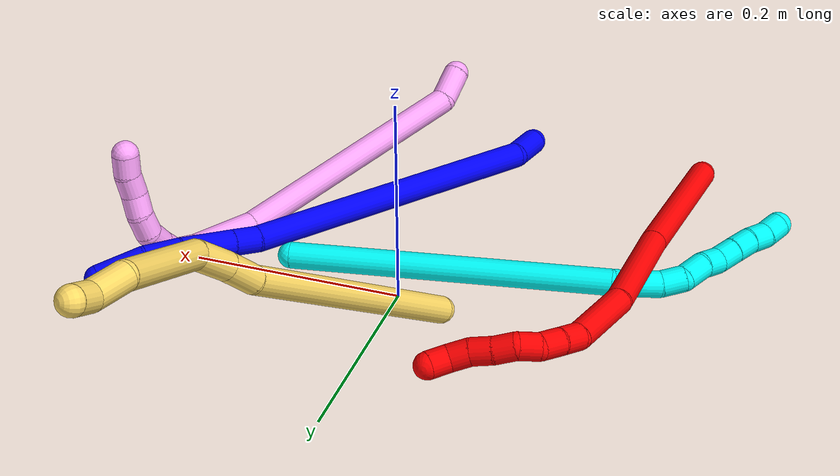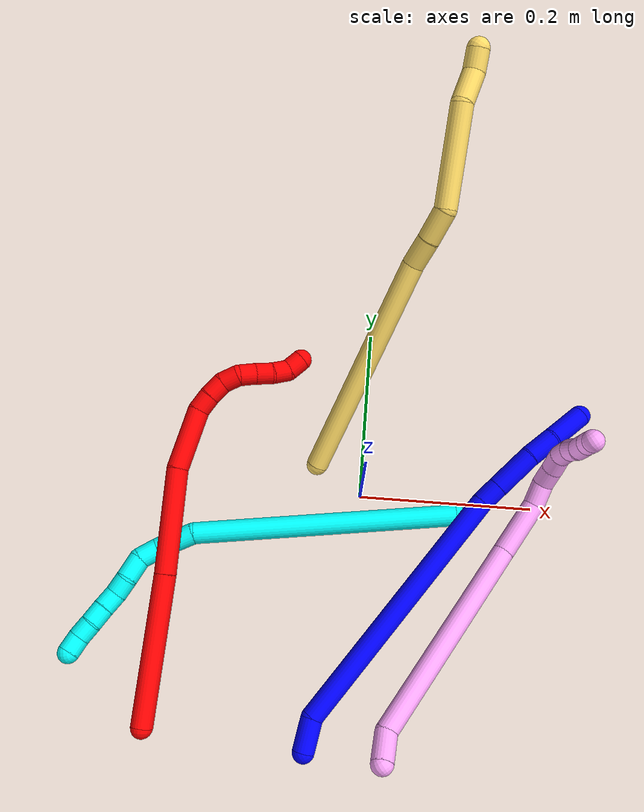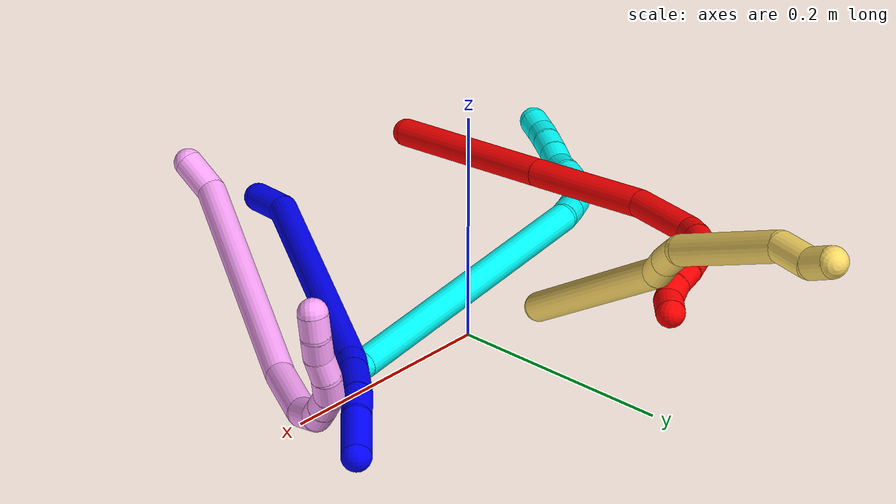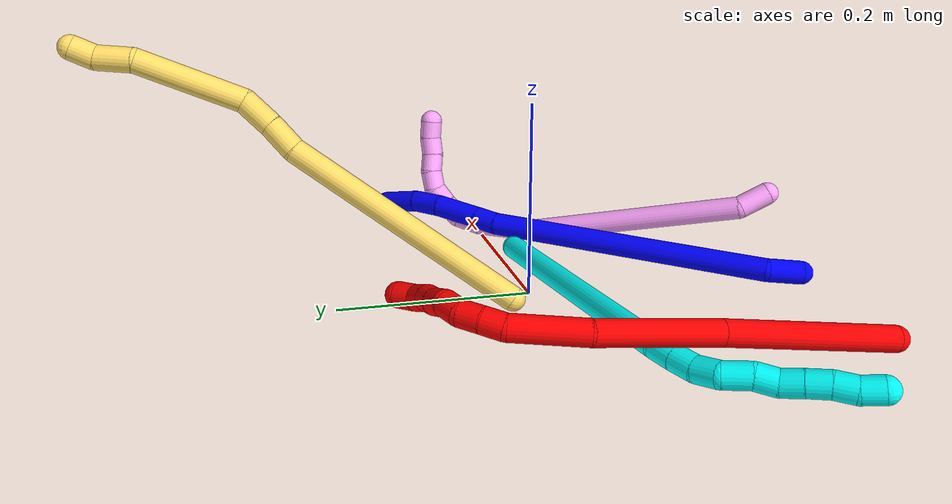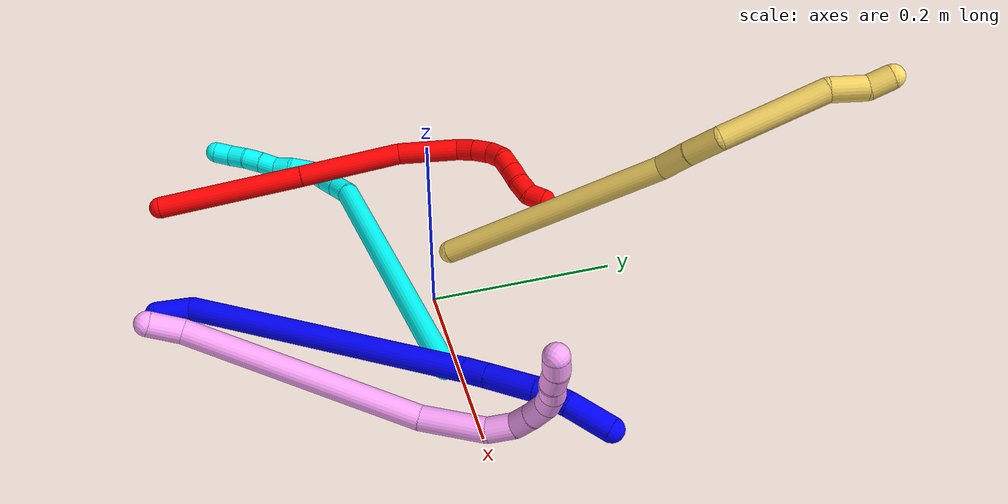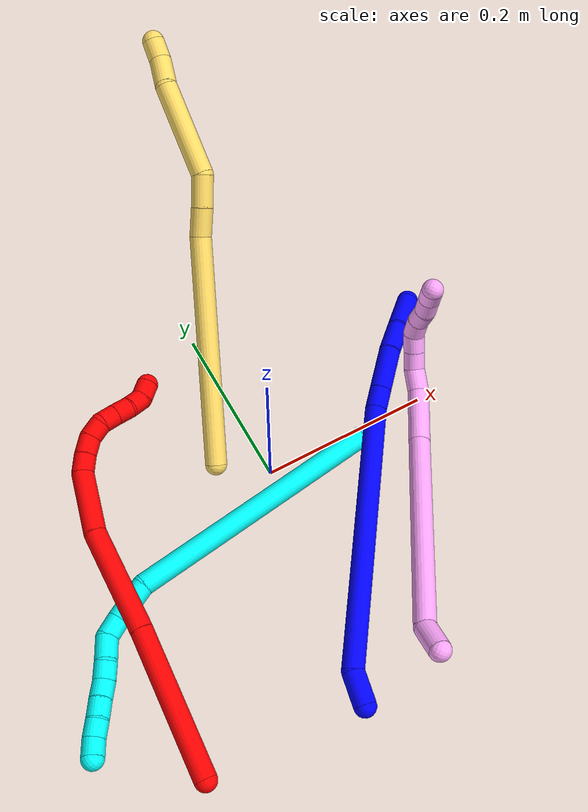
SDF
<sdf version="1.7">
 <world name="default">
  <plugin name="TubeGeneratorPlugin" filename="libtube_generator_plugin.so"/>
  <model name="photoneo_s_sensor">
   <static>1</static>
   <pose>0 0 2 1.57079 1.57079 3.14159</pose>
   <link name="link">
    <inertial><mass>0.1</mass></inertial>
    <sensor name="sensor" type="depth">
     <update_rate>30</update_rate>
     <camera>
      <horizontal_fov>1.22</horizontal_fov>
      <image><width>1920</width><height>1200</height><format>B8G8R8</format></image>
      <clip><near>0.1</near><far>4</far></clip>
      <depth_camera><output>points</output></depth_camera>
     </camera>
     <plugin name="camera_plugin" filename="libgazebo_ros_depth_camera.so">
      <baseline>0.2</baseline>
      <alwaysOn>1</alwaysOn>
      <updateRate>0.0</updateRate>
      <cameraName>camera_ir</cameraName>
      <imageTopicName>/camera/color/image_raw</imageTopicName>
      <cameraInfoTopicName>/camera/color/camera_info</cameraInfoTopicName>
      <depthImageTopicName>/camera/depth/image_raw</depthImageTopicName>
      <depthImageCameraInfoTopicName>/camera/depth/camera_info</depthImageCameraInfoTopicName>
      <pointCloudTopicName>/camera/depth/points</pointCloudTopicName>
      <frameName>fr_optical</frameName>
      <pointCloudCutoff>0.1</pointCloudCutoff>
      <pointCloudCutoffMax>2.0</pointCloudCutoffMax>
      <distortionK1>0</distortionK1>
      <distortionK2>0</distortionK2>
      <distortionK3>0</distortionK3>
      <distortionT1>0</distortionT1>
      <distortionT2>0</distortionT2>
      <CxPrime>0</CxPrime>
      <Cx>0</Cx>
      <Cy>0</Cy>
      <focalLength>0</focalLength>
      <hackBaseline>0</hackBaseline>
     </plugin>
    </sensor>
   </link>
  </model>
  <gravity>0 0 -9.8</gravity>
  <magnetic_field>6e-06 2.3e-05 -4.2e-05</magnetic_field>
  <atmosphere type="adiabatic"/>
  <physics name="default_physics" default="0" type="ode">
   <max_step_size>0.003</max_step_size>
   <real_time_factor>1</real_time_factor>
   <real_time_update_rate>1000</real_time_update_rate>
   <max_contacts>10000</max_contacts>
   <ode>
    <solver>
     <type>quick</type>
     <iters>100</iters>
     <sor>1.3</sor>
     <use_dynamic_moi_rescaling>0</use_dynamic_moi_rescaling>
    </solver>
    <constraints>
     <contact_max_correcting_vel>0</contact_max_correcting_vel>
     <contact_surface_layer>0.001</contact_surface_layer>
     <cfm>0</cfm>
     <erp>0.2</erp>
    </constraints>
   </ode>
  </physics>
  <scene><ambient>0.4 0.4 0.4 1</ambient><background>0.7 0.7 0.7 1</background><shadows>0</shadows></scene>
  <audio><device>default</device></audio>
  <spherical_coordinates>
   <surface_model>EARTH_WGS84</surface_model>
   <latitude_deg>0</latitude_deg>
   <longitude_deg>0</longitude_deg>
   <elevation>0</elevation>
   <heading_deg>0</heading_deg>
  </spherical_coordinates>
  <model name="bin">
   <static>1</static>
   <link name="bottom">
    <collision name="collision-bottom">
     <pose>0 0 -0.01 0 -0 0</pose>
     <geometry><box><size>0.8 0.6 0.02</size></box></geometry>
     <surface>
      <friction><ode><mu>100</mu><mu2>100</mu2></ode></friction>
      <contact><collide_bitmask>65535</collide_bitmask></contact>
     </surface>
    </collision>
   </link>
   <link name="west_wall">
    <collision name="collision-west_wall">
     <pose>-0.41 0 0.1 0 -0 0</pose>
     <geometry><box><size>0.02 0.6 0.2</size></box></geometry>
     <surface>
      <friction><ode><mu>100</mu><mu2>100</mu2></ode></friction>
      <contact><collide_bitmask>65535</collide_bitmask></contact>
     </surface>
    </collision>
   </link>
   <link name="east_wall">
    <collision name="collision-east_wall">
     <pose>0.41 0 0.1 0 -0 0</pose>
     <geometry><box><size>0.02 0.6 0.2</size></box></geometry>
     <surface>
      <friction><ode><mu>100</mu><mu2>100</mu2></ode></friction>
      <contact><collide_bitmask>65535</collide_bitmask></contact>
     </surface>
    </collision>
   </link>
   <link name="south_wall">
    <collision name="collision-south_wall">
     <pose>0 -0.31 0.1 0 -0 0</pose>
     <geometry><box><size>0.8 0.02 0.2</size></box></geometry>
     <surface>
      <friction><ode><mu>100</mu><mu2>100</mu2></ode></friction>
      <contact><collide_bitmask>65535</collide_bitmask></contact>
     </surface>
    </collision>
   </link>
   <link name="north_wall">
    <collision name="collision-north_wall">
     <pose>0 0.31 0.1 0 -0 0</pose>
     <geometry><box><size>0.8 0.02 0.2</size></box></geometry>
     <surface>
      <friction><ode><mu>100</mu><mu2>100</mu2></ode></friction>
      <contact><collide_bitmask>65535</collide_bitmask></contact>
     </surface>
    </collision>
   </link>
  </model>
  <model name="1">
   <static>0</static>
   <link name="1">
    <collision name="collision-cylinder-e_1_1_4">
     <pose>0.009409 0.008324 0.014141 -0.532038 0.520663 -0.144909</pose>
     <geometry><cylinder><radius>0.0125</radius><length>0.03783</length></cylinder></geometry>
     <surface>
      <friction><ode><mu>1.16</mu><mu2>1.16</mu2><slip1>0</slip1><slip2>0</slip2></ode></friction>
      <contact><ode><kp>1e+06</kp><kd>1</kd><max_vel>0</max_vel><min_depth>0.001</min_depth></ode></contact>
     </surface>
    </collision>
    <visual name="visual-cylinder-e_1_1_4">
     <pose>0.009409 0.008324 0.014141 -0.532038 0.520663 -0.144909</pose>
     <geometry><cylinder><radius>0.0125</radius><length>0.03783</length></cylinder></geometry>
     <material><ambient>0 0 1 1</ambient></material>
    </visual>
    <collision name="collision-cylinder-e_2_4_5">
     <pose>0.120725 0.112484 0.089419 -1.00294 0.730855 -0.413513</pose>
     <geometry><cylinder><radius>0.0125</radius><length>0.305333</length></cylinder></geometry>
     <surface>
      <friction><ode><mu>1.16</mu><mu2>1.16</mu2><slip1>0</slip1><slip2>0</slip2></ode></friction>
      <contact><ode><kp>1e+06</kp><kd>1</kd><max_vel>0</max_vel><min_depth>0.001</min_depth></ode></contact>
     </surface>
    </collision>
    <visual name="visual-cylinder-e_2_4_5">
     <pose>0.120725 0.112484 0.089419 -1.00294 0.730855 -0.413513</pose>
     <geometry><cylinder><radius>0.0125</radius><length>0.305333</length></cylinder></geometry>
     <material><ambient>0 0 1 1</ambient></material>
    </visual>
    <collision name="collision-cylinder-e_3_5_6">
     <pose>0.232304 0.215613 0.154128 -1.11548 0.872401 -0.565961</pose>
     <geometry><cylinder><radius>0.0125</radius><length>0.025261</length></cylinder></geometry>
     <surface>
      <friction><ode><mu>1.16</mu><mu2>1.16</mu2><slip1>0</slip1><slip2>0</slip2></ode></friction>
      <contact><ode><kp>1e+06</kp><kd>1</kd><max_vel>0</max_vel><min_depth>0.001</min_depth></ode></contact>
     </surface>
    </collision>
    <visual name="visual-cylinder-e_3_5_6">
     <pose>0.232304 0.215613 0.154128 -1.11548 0.872401 -0.565961</pose>
     <geometry><cylinder><radius>0.0125</radius><length>0.025261</length></cylinder></geometry>
     <material><ambient>0 0 1 1</ambient></material>
    </visual>
    <collision name="collision-cylinder-e_4_6_7">
     <pose>0.261457 0.238038 0.164852 -1.1292 0.861001 -0.566105</pose>
     <geometry><cylinder><radius>0.0125</radius><length>0.051365</length></cylinder></geometry>
     <surface>
      <friction><ode><mu>1.16</mu><mu2>1.16</mu2><slip1>0</slip1><slip2>0</slip2></ode></friction>
      <contact><ode><kp>1e+06</kp><kd>1</kd><max_vel>0</max_vel><min_depth>0.001</min_depth></ode></contact>
     </surface>
    </collision>
    <visual name="visual-cylinder-e_4_6_7">
     <pose>0.261457 0.238038 0.164852 -1.1292 0.861001 -0.566105</pose>
     <geometry><cylinder><radius>0.0125</radius><length>0.051365</length></cylinder></geometry>
     <material><ambient>0 0 1 1</ambient></material>
    </visual>
    <collision name="collision-cylinder-e_5_7_8">
     <pose>0.292833 0.265022 0.175202 -1.30732 0.769615 -0.601625</pose>
     <geometry><cylinder><radius>0.0125</radius><length>0.034188</length></cylinder></geometry>
     <surface>
      <friction><ode><mu>1.16</mu><mu2>1.16</mu2><slip1>0</slip1><slip2>0</slip2></ode></friction>
      <contact><ode><kp>1e+06</kp><kd>1</kd><max_vel>0</max_vel><min_depth>0.001</min_depth></ode></contact>
     </surface>
    </collision>
    <visual name="visual-cylinder-e_5_7_8">
     <pose>0.292833 0.265022 0.175202 -1.30732 0.769615 -0.601625</pose>
     <geometry><cylinder><radius>0.0125</radius><length>0.034188</length></cylinder></geometry>
     <material><ambient>0 0 1 1</ambient></material>
    </visual>
    <collision name="collision-cylinder-e_6_8_2">
     <pose>0.317266 0.295692 0.182671 -1.34757 0.576219 -0.464692</pose>
     <geometry><cylinder><radius>0.0125</radius><length>0.046022</length></cylinder></geometry>
     <surface>
      <friction><ode><mu>1.16</mu><mu2>1.16</mu2><slip1>0</slip1><slip2>0</slip2></ode></friction>
      <contact><ode><kp>1e+06</kp><kd>1</kd><max_vel>0</max_vel><min_depth>0.001</min_depth></ode></contact>
     </surface>
    </collision>
    <visual name="visual-cylinder-e_6_8_2">
     <pose>0.317266 0.295692 0.182671 -1.34757 0.576219 -0.464692</pose>
     <geometry><cylinder><radius>0.0125</radius><length>0.046022</length></cylinder></geometry>
     <material><ambient>0 0 1 1</ambient></material>
    </visual>
    <collision name="collision-sphere-2">
     <pose>0.329803 0.314509 0.186943 0 -0 0</pose>
     <geometry><sphere><radius>0.0125</radius></sphere></geometry>
     <surface>
      <friction><ode><mu>1.16</mu><mu2>1.16</mu2><slip1>0</slip1><slip2>0</slip2></ode></friction>
      <contact><ode><kp>1e+06</kp><kd>1</kd><max_vel>0</max_vel><min_depth>0.001</min_depth></ode></contact>
     </surface>
    </collision>
    <visual name="visual-sphere-2">
     <pose>0.329803 0.314509 0.186943 0 -0 0</pose>
     <geometry><sphere><radius>0.0125</radius></sphere></geometry>
     <material><ambient>0 0 1 1</ambient></material>
    </visual>
    <collision name="collision-sphere-4">
     <pose>0.018819 0.016648 0.028281 0 -0 0</pose>
     <geometry><sphere><radius>0.0125</radius></sphere></geometry>
     <surface>
      <friction><ode><mu>1.16</mu><mu2>1.16</mu2><slip1>0</slip1><slip2>0</slip2></ode></friction>
      <contact><ode><kp>1e+06</kp><kd>1</kd><max_vel>0</max_vel><min_depth>0.001</min_depth></ode></contact>
     </surface>
    </collision>
    <visual name="visual-sphere-4">
     <pose>0.018819 0.016648 0.028281 0 -0 0</pose>
     <geometry><sphere><radius>0.0125</radius></sphere></geometry>
     <material><ambient>0 0 1 1</ambient></material>
    </visual>
    <collision name="collision-sphere-1">
     <geometry><sphere><radius>0.0125</radius></sphere></geometry>
     <surface>
      <friction><ode><mu>1.16</mu><mu2>1.16</mu2><slip1>0</slip1><slip2>0</slip2></ode></friction>
      <contact><ode><kp>1e+06</kp><kd>1</kd><max_vel>0</max_vel><min_depth>0.001</min_depth></ode></contact>
     </surface>
    </collision>
    <visual name="visual-sphere-1">
     <geometry><sphere><radius>0.0125</radius></sphere></geometry>
     <material><ambient>0 0 1 1</ambient></material>
    </visual>
    <collision name="collision-sphere-8">
     <pose>0.304728 0.276875 0.1784 0 -0 0</pose>
     <geometry><sphere><radius>0.0125</radius></sphere></geometry>
     <surface>
      <friction><ode><mu>1.16</mu><mu2>1.16</mu2><slip1>0</slip1><slip2>0</slip2></ode></friction>
      <contact><ode><kp>1e+06</kp><kd>1</kd><max_vel>0</max_vel><min_depth>0.001</min_depth></ode></contact>
     </surface>
    </collision>
    <visual name="visual-sphere-8">
     <pose>0.304728 0.276875 0.1784 0 -0 0</pose>
     <geometry><sphere><radius>0.0125</radius></sphere></geometry>
     <material><ambient>0 0 1 1</ambient></material>
    </visual>
    <collision name="collision-sphere-5">
     <pose>0.22263 0.208319 0.150556 0 -0 0</pose>
     <geometry><sphere><radius>0.0125</radius></sphere></geometry>
     <surface>
      <friction><ode><mu>1.16</mu><mu2>1.16</mu2><slip1>0</slip1><slip2>0</slip2></ode></friction>
      <contact><ode><kp>1e+06</kp><kd>1</kd><max_vel>0</max_vel><min_depth>0.001</min_depth></ode></contact>
     </surface>
    </collision>
    <visual name="visual-sphere-5">
     <pose>0.22263 0.208319 0.150556 0 -0 0</pose>
     <geometry><sphere><radius>0.0125</radius></sphere></geometry>
     <material><ambient>0 0 1 1</ambient></material>
    </visual>
    <collision name="collision-sphere-6">
     <pose>0.241978 0.222907 0.157699 0 -0 0</pose>
     <geometry><sphere><radius>0.0125</radius></sphere></geometry>
     <surface>
      <friction><ode><mu>1.16</mu><mu2>1.16</mu2><slip1>0</slip1><slip2>0</slip2></ode></friction>
      <contact><ode><kp>1e+06</kp><kd>1</kd><max_vel>0</max_vel><min_depth>0.001</min_depth></ode></contact>
     </surface>
    </collision>
    <visual name="visual-sphere-6">
     <pose>0.241978 0.222907 0.157699 0 -0 0</pose>
     <geometry><sphere><radius>0.0125</radius></sphere></geometry>
     <material><ambient>0 0 1 1</ambient></material>
    </visual>
    <collision name="collision-sphere-7">
     <pose>0.280937 0.253169 0.172005 0 -0 0</pose>
     <geometry><sphere><radius>0.0125</radius></sphere></geometry>
     <surface>
      <friction><ode><mu>1.16</mu><mu2>1.16</mu2><slip1>0</slip1><slip2>0</slip2></ode></friction>
      <contact><ode><kp>1e+06</kp><kd>1</kd><max_vel>0</max_vel><min_depth>0.001</min_depth></ode></contact>
     </surface>
    </collision>
    <visual name="visual-sphere-7">
     <pose>0.280937 0.253169 0.172005 0 -0 0</pose>
     <geometry><sphere><radius>0.0125</radius></sphere></geometry>
     <material><ambient>0 0 1 1</ambient></material>
    </visual>
    <inertial>
     <pose>0.162256 0.150005 0.109191 0 -0 0</pose>
     <mass>0.5</mass>
     <inertia>
      <ixx>0.00095</ixx>
      <ixy>0</ixy>
      <ixz>0</ixz>
      <iyy>0.001036</iyy>
      <iyz>0</iyz>
      <izz>-0.00312</izz>
     </inertia>
    </inertial>
   </link>
   <pose>-0.043152 -0.287633 0.013548 -1.45466 -0.770931 0.467163</pose>
  </model>
  <model name="2">
   <static>0</static>
   <link name="2">
    <collision name="collision-cylinder-e_1_1_4">
     <pose>0.007482 -0.00672 -0.082934 3.06074 0.089686 1.67441</pose>
     <geometry><cylinder><radius>0.0125</radius><length>0.167083</length></cylinder></geometry>
     <surface>
      <friction><ode><mu>1.16</mu><mu2>1.16</mu2><slip1>0</slip1><slip2>0</slip2></ode></friction>
      <contact><ode><kp>1e+06</kp><kd>1</kd><max_vel>0</max_vel><min_depth>0.001</min_depth></ode></contact>
     </surface>
    </collision>
    <visual name="visual-cylinder-e_1_1_4">
     <pose>0.007482 -0.00672 -0.082934 3.06074 0.089686 1.67441</pose>
     <geometry><cylinder><radius>0.0125</radius><length>0.167083</length></cylinder></geometry>
     <material><ambient>1 0 0 1</ambient></material>
    </visual>
    <collision name="collision-cylinder-e_2_4_5">
     <pose>0.018629 -0.020256 -0.224763 3.02637 0.061717 0.982854</pose>
     <geometry><cylinder><radius>0.0125</radius><length>0.118803</length></cylinder></geometry>
     <surface>
      <friction><ode><mu>1.16</mu><mu2>1.16</mu2><slip1>0</slip1><slip2>0</slip2></ode></friction>
      <contact><ode><kp>1e+06</kp><kd>1</kd><max_vel>0</max_vel><min_depth>0.001</min_depth></ode></contact>
     </surface>
    </collision>
    <visual name="visual-cylinder-e_2_4_5">
     <pose>0.018629 -0.020256 -0.224763 3.02637 0.061717 0.982854</pose>
     <geometry><cylinder><radius>0.0125</radius><length>0.118803</length></cylinder></geometry>
     <material><ambient>1 0 0 1</ambient></material>
    </visual>
    <collision name="collision-cylinder-e_3_5_6">
     <pose>0.032055 -0.028307 -0.318168 3.10585 0.275527 2.88517</pose>
     <geometry><cylinder><radius>0.0125</radius><length>0.07177</length></cylinder></geometry>
     <surface>
      <friction><ode><mu>1.16</mu><mu2>1.16</mu2><slip1>0</slip1><slip2>0</slip2></ode></friction>
      <contact><ode><kp>1e+06</kp><kd>1</kd><max_vel>0</max_vel><min_depth>0.001</min_depth></ode></contact>
     </surface>
    </collision>
    <visual name="visual-cylinder-e_3_5_6">
     <pose>0.032055 -0.028307 -0.318168 3.10585 0.275527 2.88517</pose>
     <geometry><cylinder><radius>0.0125</radius><length>0.07177</length></cylinder></geometry>
     <material><ambient>1 0 0 1</ambient></material>
    </visual>
    <collision name="collision-cylinder-e_4_6_7">
     <pose>0.04684 -0.027119 -0.361544 -2.87496 0.500113 -2.17455</pose>
     <geometry><cylinder><radius>0.0125</radius><length>0.020948</length></cylinder></geometry>
     <surface>
      <friction><ode><mu>1.16</mu><mu2>1.16</mu2><slip1>0</slip1><slip2>0</slip2></ode></friction>
      <contact><ode><kp>1e+06</kp><kd>1</kd><max_vel>0</max_vel><min_depth>0.001</min_depth></ode></contact>
     </surface>
    </collision>
    <visual name="visual-cylinder-e_4_6_7">
     <pose>0.04684 -0.027119 -0.361544 -2.87496 0.500113 -2.17455</pose>
     <geometry><cylinder><radius>0.0125</radius><length>0.020948</length></cylinder></geometry>
     <material><ambient>1 0 0 1</ambient></material>
    </visual>
    <collision name="collision-cylinder-e_5_7_8">
     <pose>0.05815 -0.022311 -0.378638 -2.85927 0.633084 -2.32292</pose>
     <geometry><cylinder><radius>0.0125</radius><length>0.021252</length></cylinder></geometry>
     <surface>
      <friction><ode><mu>1.16</mu><mu2>1.16</mu2><slip1>0</slip1><slip2>0</slip2></ode></friction>
      <contact><ode><kp>1e+06</kp><kd>1</kd><max_vel>0</max_vel><min_depth>0.001</min_depth></ode></contact>
     </surface>
    </collision>
    <visual name="visual-cylinder-e_5_7_8">
     <pose>0.05815 -0.022311 -0.378638 -2.85927 0.633084 -2.32292</pose>
     <geometry><cylinder><radius>0.0125</radius><length>0.021252</length></cylinder></geometry>
     <material><ambient>1 0 0 1</ambient></material>
    </visual>
    <collision name="collision-cylinder-e_6_8_9">
     <pose>0.072026 -0.015521 -0.391789 -2.41189 0.854708 -1.74583</pose>
     <geometry><cylinder><radius>0.0125</radius><length>0.020121</length></cylinder></geometry>
     <surface>
      <friction><ode><mu>1.16</mu><mu2>1.16</mu2><slip1>0</slip1><slip2>0</slip2></ode></friction>
      <contact><ode><kp>1e+06</kp><kd>1</kd><max_vel>0</max_vel><min_depth>0.001</min_depth></ode></contact>
     </surface>
    </collision>
    <visual name="visual-cylinder-e_6_8_9">
     <pose>0.072026 -0.015521 -0.391789 -2.41189 0.854708 -1.74583</pose>
     <geometry><cylinder><radius>0.0125</radius><length>0.020121</length></cylinder></geometry>
     <material><ambient>1 0 0 1</ambient></material>
    </visual>
    <collision name="collision-cylinder-e_7_9_10">
     <pose>0.089345 -0.009811 -0.39867 -2.55306 1.33335 -2.40629</pose>
     <geometry><cylinder><radius>0.0125</radius><length>0.02002</length></cylinder></geometry>
     <surface>
      <friction><ode><mu>1.16</mu><mu2>1.16</mu2><slip1>0</slip1><slip2>0</slip2></ode></friction>
      <contact><ode><kp>1e+06</kp><kd>1</kd><max_vel>0</max_vel><min_depth>0.001</min_depth></ode></contact>
     </surface>
    </collision>
    <visual name="visual-cylinder-e_7_9_10">
     <pose>0.089345 -0.009811 -0.39867 -2.55306 1.33335 -2.40629</pose>
     <geometry><cylinder><radius>0.0125</radius><length>0.02002</length></cylinder></geometry>
     <material><ambient>1 0 0 1</ambient></material>
    </visual>
    <collision name="collision-cylinder-e_8_10_11">
     <pose>0.108653 -0.005938 -0.40192 -2.03722 1.27939 -1.75838</pose>
     <geometry><cylinder><radius>0.0125</radius><length>0.020001</length></cylinder></geometry>
     <surface>
      <friction><ode><mu>1.16</mu><mu2>1.16</mu2><slip1>0</slip1><slip2>0</slip2></ode></friction>
      <contact><ode><kp>1e+06</kp><kd>1</kd><max_vel>0</max_vel><min_depth>0.001</min_depth></ode></contact>
     </surface>
    </collision>
    <visual name="visual-cylinder-e_8_10_11">
     <pose>0.108653 -0.005938 -0.40192 -2.03722 1.27939 -1.75838</pose>
     <geometry><cylinder><radius>0.0125</radius><length>0.020001</length></cylinder></geometry>
     <material><ambient>1 0 0 1</ambient></material>
    </visual>
    <collision name="collision-cylinder-e_9_11_12">
     <pose>0.127828 -0.002774 -0.405963 -2.92738 1.28548 -2.85637</pose>
     <geometry><cylinder><radius>0.0125</radius><length>0.020001</length></cylinder></geometry>
     <surface>
      <friction><ode><mu>1.16</mu><mu2>1.16</mu2><slip1>0</slip1><slip2>0</slip2></ode></friction>
      <contact><ode><kp>1e+06</kp><kd>1</kd><max_vel>0</max_vel><min_depth>0.001</min_depth></ode></contact>
     </surface>
    </collision>
    <visual name="visual-cylinder-e_9_11_12">
     <pose>0.127828 -0.002774 -0.405963 -2.92738 1.28548 -2.85637</pose>
     <geometry><cylinder><radius>0.0125</radius><length>0.020001</length></cylinder></geometry>
     <material><ambient>1 0 0 1</ambient></material>
    </visual>
    <collision name="collision-cylinder-e_10_12_2">
     <pose>0.144542 -0.000867 -0.415614 -2.95422 0.792017 -2.69945</pose>
     <geometry><cylinder><radius>0.0125</radius><length>0.02</length></cylinder></geometry>
     <surface>
      <friction><ode><mu>1.16</mu><mu2>1.16</mu2><slip1>0</slip1><slip2>0</slip2></ode></friction>
      <contact><ode><kp>1e+06</kp><kd>1</kd><max_vel>0</max_vel><min_depth>0.001</min_depth></ode></contact>
     </surface>
    </collision>
    <visual name="visual-cylinder-e_10_12_2">
     <pose>0.144542 -0.000867 -0.415614 -2.95422 0.792017 -2.69945</pose>
     <geometry><cylinder><radius>0.0125</radius><length>0.02</length></cylinder></geometry>
     <material><ambient>1 0 0 1</ambient></material>
    </visual>
    <collision name="collision-sphere-2">
     <pose>0.151659 0.000442 -0.422515 0 -0 0</pose>
     <geometry><sphere><radius>0.0125</radius></sphere></geometry>
     <surface>
      <friction><ode><mu>1.16</mu><mu2>1.16</mu2><slip1>0</slip1><slip2>0</slip2></ode></friction>
      <contact><ode><kp>1e+06</kp><kd>1</kd><max_vel>0</max_vel><min_depth>0.001</min_depth></ode></contact>
     </surface>
    </collision>
    <visual name="visual-sphere-2">
     <pose>0.151659 0.000442 -0.422515 0 -0 0</pose>
     <geometry><sphere><radius>0.0125</radius></sphere></geometry>
     <material><ambient>1 0 0 1</ambient></material>
    </visual>
    <collision name="collision-sphere-12">
     <pose>0.137424 -0.002175 -0.408713 0 -0 0</pose>
     <geometry><sphere><radius>0.0125</radius></sphere></geometry>
     <surface>
      <friction><ode><mu>1.16</mu><mu2>1.16</mu2><slip1>0</slip1><slip2>0</slip2></ode></friction>
      <contact><ode><kp>1e+06</kp><kd>1</kd><max_vel>0</max_vel><min_depth>0.001</min_depth></ode></contact>
     </surface>
    </collision>
    <visual name="visual-sphere-12">
     <pose>0.137424 -0.002175 -0.408713 0 -0 0</pose>
     <geometry><sphere><radius>0.0125</radius></sphere></geometry>
     <material><ambient>1 0 0 1</ambient></material>
    </visual>
    <collision name="collision-sphere-11">
     <pose>0.118232 -0.003372 -0.403212 0 -0 0</pose>
     <geometry><sphere><radius>0.0125</radius></sphere></geometry>
     <surface>
      <friction><ode><mu>1.16</mu><mu2>1.16</mu2><slip1>0</slip1><slip2>0</slip2></ode></friction>
      <contact><ode><kp>1e+06</kp><kd>1</kd><max_vel>0</max_vel><min_depth>0.001</min_depth></ode></contact>
     </surface>
    </collision>
    <visual name="visual-sphere-11">
     <pose>0.118232 -0.003372 -0.403212 0 -0 0</pose>
     <geometry><sphere><radius>0.0125</radius></sphere></geometry>
     <material><ambient>1 0 0 1</ambient></material>
    </visual>
    <collision name="collision-sphere-10">
     <pose>0.099074 -0.008504 -0.400628 0 -0 0</pose>
     <geometry><sphere><radius>0.0125</radius></sphere></geometry>
     <surface>
      <friction><ode><mu>1.16</mu><mu2>1.16</mu2><slip1>0</slip1><slip2>0</slip2></ode></friction>
      <contact><ode><kp>1e+06</kp><kd>1</kd><max_vel>0</max_vel><min_depth>0.001</min_depth></ode></contact>
     </surface>
    </collision>
    <visual name="visual-sphere-10">
     <pose>0.099074 -0.008504 -0.400628 0 -0 0</pose>
     <geometry><sphere><radius>0.0125</radius></sphere></geometry>
     <material><ambient>1 0 0 1</ambient></material>
    </visual>
    <collision name="collision-sphere-9">
     <pose>0.079616 -0.011119 -0.396711 0 -0 0</pose>
     <geometry><sphere><radius>0.0125</radius></sphere></geometry>
     <surface>
      <friction><ode><mu>1.16</mu><mu2>1.16</mu2><slip1>0</slip1><slip2>0</slip2></ode></friction>
      <contact><ode><kp>1e+06</kp><kd>1</kd><max_vel>0</max_vel><min_depth>0.001</min_depth></ode></contact>
     </surface>
    </collision>
    <visual name="visual-sphere-9">
     <pose>0.079616 -0.011119 -0.396711 0 -0 0</pose>
     <geometry><sphere><radius>0.0125</radius></sphere></geometry>
     <material><ambient>1 0 0 1</ambient></material>
    </visual>
    <collision name="collision-sphere-4">
     <pose>0.014965 -0.01344 -0.165868 0 -0 0</pose>
     <geometry><sphere><radius>0.0125</radius></sphere></geometry>
     <surface>
      <friction><ode><mu>1.16</mu><mu2>1.16</mu2><slip1>0</slip1><slip2>0</slip2></ode></friction>
      <contact><ode><kp>1e+06</kp><kd>1</kd><max_vel>0</max_vel><min_depth>0.001</min_depth></ode></contact>
     </surface>
    </collision>
    <visual name="visual-sphere-4">
     <pose>0.014965 -0.01344 -0.165868 0 -0 0</pose>
     <geometry><sphere><radius>0.0125</radius></sphere></geometry>
     <material><ambient>1 0 0 1</ambient></material>
    </visual>
    <collision name="collision-sphere-1">
     <geometry><sphere><radius>0.0125</radius></sphere></geometry>
     <surface>
      <friction><ode><mu>1.16</mu><mu2>1.16</mu2><slip1>0</slip1><slip2>0</slip2></ode></friction>
      <contact><ode><kp>1e+06</kp><kd>1</kd><max_vel>0</max_vel><min_depth>0.001</min_depth></ode></contact>
     </surface>
    </collision>
    <visual name="visual-sphere-1">
     <geometry><sphere><radius>0.0125</radius></sphere></geometry>
     <material><ambient>1 0 0 1</ambient></material>
    </visual>
    <collision name="collision-sphere-8">
     <pose>0.064437 -0.019924 -0.386866 0 -0 0</pose>
     <geometry><sphere><radius>0.0125</radius></sphere></geometry>
     <surface>
      <friction><ode><mu>1.16</mu><mu2>1.16</mu2><slip1>0</slip1><slip2>0</slip2></ode></friction>
      <contact><ode><kp>1e+06</kp><kd>1</kd><max_vel>0</max_vel><min_depth>0.001</min_depth></ode></contact>
     </surface>
    </collision>
    <visual name="visual-sphere-8">
     <pose>0.064437 -0.019924 -0.386866 0 -0 0</pose>
     <geometry><sphere><radius>0.0125</radius></sphere></geometry>
     <material><ambient>1 0 0 1</ambient></material>
    </visual>
    <collision name="collision-sphere-5">
     <pose>0.022293 -0.027073 -0.283659 0 -0 0</pose>
     <geometry><sphere><radius>0.0125</radius></sphere></geometry>
     <surface>
      <friction><ode><mu>1.16</mu><mu2>1.16</mu2><slip1>0</slip1><slip2>0</slip2></ode></friction>
      <contact><ode><kp>1e+06</kp><kd>1</kd><max_vel>0</max_vel><min_depth>0.001</min_depth></ode></contact>
     </surface>
    </collision>
    <visual name="visual-sphere-5">
     <pose>0.022293 -0.027073 -0.283659 0 -0 0</pose>
     <geometry><sphere><radius>0.0125</radius></sphere></geometry>
     <material><ambient>1 0 0 1</ambient></material>
    </visual>
    <collision name="collision-sphere-6">
     <pose>0.041818 -0.029541 -0.352678 0 -0 0</pose>
     <geometry><sphere><radius>0.0125</radius></sphere></geometry>
     <surface>
      <friction><ode><mu>1.16</mu><mu2>1.16</mu2><slip1>0</slip1><slip2>0</slip2></ode></friction>
      <contact><ode><kp>1e+06</kp><kd>1</kd><max_vel>0</max_vel><min_depth>0.001</min_depth></ode></contact>
     </surface>
    </collision>
    <visual name="visual-sphere-6">
     <pose>0.041818 -0.029541 -0.352678 0 -0 0</pose>
     <geometry><sphere><radius>0.0125</radius></sphere></geometry>
     <material><ambient>1 0 0 1</ambient></material>
    </visual>
    <collision name="collision-sphere-7">
     <pose>0.051863 -0.024697 -0.370411 0 -0 0</pose>
     <geometry><sphere><radius>0.0125</radius></sphere></geometry>
     <surface>
      <friction><ode><mu>1.16</mu><mu2>1.16</mu2><slip1>0</slip1><slip2>0</slip2></ode></friction>
      <contact><ode><kp>1e+06</kp><kd>1</kd><max_vel>0</max_vel><min_depth>0.001</min_depth></ode></contact>
     </surface>
    </collision>
    <visual name="visual-sphere-7">
     <pose>0.051863 -0.024697 -0.370411 0 -0 0</pose>
     <geometry><sphere><radius>0.0125</radius></sphere></geometry>
     <material><ambient>1 0 0 1</ambient></material>
    </visual>
    <inertial>
     <pose>0.037679 -0.014607 -0.238701 0 -0 0</pose>
     <mass>0.5</mass>
     <inertia>
      <ixx>0.000532</ixx>
      <ixy>0</ixy>
      <ixz>0</ixz>
      <iyy>0.000522</iyy>
      <iyz>0</iyz>
      <izz>-4.7e-05</izz>
     </inertia>
    </inertial>
   </link>
   <pose>-0.221554 -0.27511 0.0163 1.82307 0.462363 0.100735</pose>
  </model>
  <model name="3">
   <static>0</static>
   <link name="3">
    <collision name="collision-cylinder-e_1_1_4">
     <pose>-0.032639 -0.071654 0.129314 0.505994 -0.217286 -0.056384</pose>
     <geometry><cylinder><radius>0.0125</radius><length>0.302799</length></cylinder></geometry>
     <surface>
      <friction><ode><mu>1.16</mu><mu2>1.16</mu2><slip1>0</slip1><slip2>0</slip2></ode></friction>
      <contact><ode><kp>1e+06</kp><kd>1</kd><max_vel>0</max_vel><min_depth>0.001</min_depth></ode></contact>
     </surface>
    </collision>
    <visual name="visual-cylinder-e_1_1_4">
     <pose>-0.032639 -0.071654 0.129314 0.505994 -0.217286 -0.056384</pose>
     <geometry><cylinder><radius>0.0125</radius><length>0.302799</length></cylinder></geometry>
     <material><ambient>0.003922 1 0.996078 1</ambient></material>
    </visual>
    <collision name="collision-cylinder-e_2_4_5">
     <pose>-0.070382 -0.145748 0.268379 0.245176 -0.469931 -0.058971</pose>
     <geometry><cylinder><radius>0.0125</radius><length>0.022546</length></cylinder></geometry>
     <surface>
      <friction><ode><mu>1.16</mu><mu2>1.16</mu2><slip1>0</slip1><slip2>0</slip2></ode></friction>
      <contact><ode><kp>1e+06</kp><kd>1</kd><max_vel>0</max_vel><min_depth>0.001</min_depth></ode></contact>
     </surface>
    </collision>
    <visual name="visual-cylinder-e_2_4_5">
     <pose>-0.070382 -0.145748 0.268379 0.245176 -0.469931 -0.058971</pose>
     <geometry><cylinder><radius>0.0125</radius><length>0.022546</length></cylinder></geometry>
     <material><ambient>0.003922 1 0.996078 1</ambient></material>
    </visual>
    <collision name="collision-cylinder-e_3_5_6">
     <pose>-0.080954 -0.150933 0.287602 0.282034 -0.506184 -0.073399</pose>
     <geometry><cylinder><radius>0.0125</radius><length>0.022552</length></cylinder></geometry>
     <surface>
      <friction><ode><mu>1.16</mu><mu2>1.16</mu2><slip1>0</slip1><slip2>0</slip2></ode></friction>
      <contact><ode><kp>1e+06</kp><kd>1</kd><max_vel>0</max_vel><min_depth>0.001</min_depth></ode></contact>
     </surface>
    </collision>
    <visual name="visual-cylinder-e_3_5_6">
     <pose>-0.080954 -0.150933 0.287602 0.282034 -0.506184 -0.073399</pose>
     <geometry><cylinder><radius>0.0125</radius><length>0.022552</length></cylinder></geometry>
     <material><ambient>0.003922 1 0.996078 1</ambient></material>
    </visual>
    <collision name="collision-cylinder-e_4_6_7">
     <pose>-0.093652 -0.157917 0.305026 0.489792 -0.676189 -0.175285</pose>
     <geometry><cylinder><radius>0.0125</radius><length>0.023108</length></cylinder></geometry>
     <surface>
      <friction><ode><mu>1.16</mu><mu2>1.16</mu2><slip1>0</slip1><slip2>0</slip2></ode></friction>
      <contact><ode><kp>1e+06</kp><kd>1</kd><max_vel>0</max_vel><min_depth>0.001</min_depth></ode></contact>
     </surface>
    </collision>
    <visual name="visual-cylinder-e_4_6_7">
     <pose>-0.093652 -0.157917 0.305026 0.489792 -0.676189 -0.175285</pose>
     <geometry><cylinder><radius>0.0125</radius><length>0.023108</length></cylinder></geometry>
     <material><ambient>0.003922 1 0.996078 1</ambient></material>
    </visual>
    <collision name="collision-cylinder-e_5_7_8">
     <pose>-0.113091 -0.163522 0.318 0.265654 -1.16788 -0.176131</pose>
     <geometry><cylinder><radius>0.0125</radius><length>0.026543</length></cylinder></geometry>
     <surface>
      <friction><ode><mu>1.16</mu><mu2>1.16</mu2><slip1>0</slip1><slip2>0</slip2></ode></friction>
      <contact><ode><kp>1e+06</kp><kd>1</kd><max_vel>0</max_vel><min_depth>0.001</min_depth></ode></contact>
     </surface>
    </collision>
    <visual name="visual-cylinder-e_5_7_8">
     <pose>-0.113091 -0.163522 0.318 0.265654 -1.16788 -0.176131</pose>
     <geometry><cylinder><radius>0.0125</radius><length>0.026543</length></cylinder></geometry>
     <material><ambient>0.003922 1 0.996078 1</ambient></material>
    </visual>
    <collision name="collision-cylinder-e_6_8_9">
     <pose>-0.133924 -0.164234 0.328766 -0.113447 -0.980154 0.060569</pose>
     <geometry><cylinder><radius>0.0125</radius><length>0.020766</length></cylinder></geometry>
     <surface>
      <friction><ode><mu>1.16</mu><mu2>1.16</mu2><slip1>0</slip1><slip2>0</slip2></ode></friction>
      <contact><ode><kp>1e+06</kp><kd>1</kd><max_vel>0</max_vel><min_depth>0.001</min_depth></ode></contact>
     </surface>
    </collision>
    <visual name="visual-cylinder-e_6_8_9">
     <pose>-0.133924 -0.164234 0.328766 -0.113447 -0.980154 0.060569</pose>
     <geometry><cylinder><radius>0.0125</radius><length>0.020766</length></cylinder></geometry>
     <material><ambient>0.003922 1 0.996078 1</ambient></material>
    </visual>
    <collision name="collision-cylinder-e_7_9_10">
     <pose>-0.151541 -0.165972 0.338966 0.492854 -1.05859 -0.29219</pose>
     <geometry><cylinder><radius>0.0125</radius><length>0.020635</length></cylinder></geometry>
     <surface>
      <friction><ode><mu>1.16</mu><mu2>1.16</mu2><slip1>0</slip1><slip2>0</slip2></ode></friction>
      <contact><ode><kp>1e+06</kp><kd>1</kd><max_vel>0</max_vel><min_depth>0.001</min_depth></ode></contact>
     </surface>
    </collision>
    <visual name="visual-cylinder-e_7_9_10">
     <pose>-0.151541 -0.165972 0.338966 0.492854 -1.05859 -0.29219</pose>
     <geometry><cylinder><radius>0.0125</radius><length>0.020635</length></cylinder></geometry>
     <material><ambient>0.003922 1 0.996078 1</ambient></material>
    </visual>
    <collision name="collision-cylinder-e_8_10_11">
     <pose>-0.169799 -0.170186 0.348023 0.37692 -1.08011 -0.22769</pose>
     <geometry><cylinder><radius>0.0125</radius><length>0.021007</length></cylinder></geometry>
     <surface>
      <friction><ode><mu>1.16</mu><mu2>1.16</mu2><slip1>0</slip1><slip2>0</slip2></ode></friction>
      <contact><ode><kp>1e+06</kp><kd>1</kd><max_vel>0</max_vel><min_depth>0.001</min_depth></ode></contact>
     </surface>
    </collision>
    <visual name="visual-cylinder-e_8_10_11">
     <pose>-0.169799 -0.170186 0.348023 0.37692 -1.08011 -0.22769</pose>
     <geometry><cylinder><radius>0.0125</radius><length>0.021007</length></cylinder></geometry>
     <material><ambient>0.003922 1 0.996078 1</ambient></material>
    </visual>
    <collision name="collision-cylinder-e_9_11_12">
     <pose>-0.187315 -0.172694 0.358241 0.121623 -0.969738 -0.06413</pose>
     <geometry><cylinder><radius>0.0125</radius><length>0.020009</length></cylinder></geometry>
     <surface>
      <friction><ode><mu>1.16</mu><mu2>1.16</mu2><slip1>0</slip1><slip2>0</slip2></ode></friction>
      <contact><ode><kp>1e+06</kp><kd>1</kd><max_vel>0</max_vel><min_depth>0.001</min_depth></ode></contact>
     </surface>
    </collision>
    <visual name="visual-cylinder-e_9_11_12">
     <pose>-0.187315 -0.172694 0.358241 0.121623 -0.969738 -0.06413</pose>
     <geometry><cylinder><radius>0.0125</radius><length>0.020009</length></cylinder></geometry>
     <material><ambient>0.003922 1 0.996078 1</ambient></material>
    </visual>
    <collision name="collision-cylinder-e_10_12_2">
     <pose>-0.204813 -0.17485 0.367417 0.391428 -1.17619 -0.262863</pose>
     <geometry><cylinder><radius>0.0125</radius><length>0.020034</length></cylinder></geometry>
     <surface>
      <friction><ode><mu>1.16</mu><mu2>1.16</mu2><slip1>0</slip1><slip2>0</slip2></ode></friction>
      <contact><ode><kp>1e+06</kp><kd>1</kd><max_vel>0</max_vel><min_depth>0.001</min_depth></ode></contact>
     </surface>
    </collision>
    <visual name="visual-cylinder-e_10_12_2">
     <pose>-0.204813 -0.17485 0.367417 0.391428 -1.17619 -0.262863</pose>
     <geometry><cylinder><radius>0.0125</radius><length>0.020034</length></cylinder></geometry>
     <material><ambient>0.003922 1 0.996078 1</ambient></material>
    </visual>
    <collision name="collision-sphere-2">
     <pose>-0.214061 -0.176319 0.370977 0 -0 0</pose>
     <geometry><sphere><radius>0.0125</radius></sphere></geometry>
     <surface>
      <friction><ode><mu>1.16</mu><mu2>1.16</mu2><slip1>0</slip1><slip2>0</slip2></ode></friction>
      <contact><ode><kp>1e+06</kp><kd>1</kd><max_vel>0</max_vel><min_depth>0.001</min_depth></ode></contact>
     </surface>
    </collision>
    <visual name="visual-sphere-2">
     <pose>-0.214061 -0.176319 0.370977 0 -0 0</pose>
     <geometry><sphere><radius>0.0125</radius></sphere></geometry>
     <material><ambient>0.003922 1 0.996078 1</ambient></material>
    </visual>
    <collision name="collision-sphere-12">
     <pose>-0.195566 -0.173381 0.363857 0 -0 0</pose>
     <geometry><sphere><radius>0.0125</radius></sphere></geometry>
     <surface>
      <friction><ode><mu>1.16</mu><mu2>1.16</mu2><slip1>0</slip1><slip2>0</slip2></ode></friction>
      <contact><ode><kp>1e+06</kp><kd>1</kd><max_vel>0</max_vel><min_depth>0.001</min_depth></ode></contact>
     </surface>
    </collision>
    <visual name="visual-sphere-12">
     <pose>-0.195566 -0.173381 0.363857 0 -0 0</pose>
     <geometry><sphere><radius>0.0125</radius></sphere></geometry>
     <material><ambient>0.003922 1 0.996078 1</ambient></material>
    </visual>
    <collision name="collision-sphere-11">
     <pose>-0.179063 -0.172008 0.352625 0 -0 0</pose>
     <geometry><sphere><radius>0.0125</radius></sphere></geometry>
     <surface>
      <friction><ode><mu>1.16</mu><mu2>1.16</mu2><slip1>0</slip1><slip2>0</slip2></ode></friction>
      <contact><ode><kp>1e+06</kp><kd>1</kd><max_vel>0</max_vel><min_depth>0.001</min_depth></ode></contact>
     </surface>
    </collision>
    <visual name="visual-sphere-11">
     <pose>-0.179063 -0.172008 0.352625 0 -0 0</pose>
     <geometry><sphere><radius>0.0125</radius></sphere></geometry>
     <material><ambient>0.003922 1 0.996078 1</ambient></material>
    </visual>
    <collision name="collision-sphere-10">
     <pose>-0.160535 -0.168364 0.343421 0 -0 0</pose>
     <geometry><sphere><radius>0.0125</radius></sphere></geometry>
     <surface>
      <friction><ode><mu>1.16</mu><mu2>1.16</mu2><slip1>0</slip1><slip2>0</slip2></ode></friction>
      <contact><ode><kp>1e+06</kp><kd>1</kd><max_vel>0</max_vel><min_depth>0.001</min_depth></ode></contact>
     </surface>
    </collision>
    <visual name="visual-sphere-10">
     <pose>-0.160535 -0.168364 0.343421 0 -0 0</pose>
     <geometry><sphere><radius>0.0125</radius></sphere></geometry>
     <material><ambient>0.003922 1 0.996078 1</ambient></material>
    </visual>
    <collision name="collision-sphere-9">
     <pose>-0.142548 -0.16358 0.334511 0 -0 0</pose>
     <geometry><sphere><radius>0.0125</radius></sphere></geometry>
     <surface>
      <friction><ode><mu>1.16</mu><mu2>1.16</mu2><slip1>0</slip1><slip2>0</slip2></ode></friction>
      <contact><ode><kp>1e+06</kp><kd>1</kd><max_vel>0</max_vel><min_depth>0.001</min_depth></ode></contact>
     </surface>
    </collision>
    <visual name="visual-sphere-9">
     <pose>-0.142548 -0.16358 0.334511 0 -0 0</pose>
     <geometry><sphere><radius>0.0125</radius></sphere></geometry>
     <material><ambient>0.003922 1 0.996078 1</ambient></material>
    </visual>
    <collision name="collision-sphere-4">
     <pose>-0.065277 -0.143309 0.258628 0 -0 0</pose>
     <geometry><sphere><radius>0.0125</radius></sphere></geometry>
     <surface>
      <friction><ode><mu>1.16</mu><mu2>1.16</mu2><slip1>0</slip1><slip2>0</slip2></ode></friction>
      <contact><ode><kp>1e+06</kp><kd>1</kd><max_vel>0</max_vel><min_depth>0.001</min_depth></ode></contact>
     </surface>
    </collision>
    <visual name="visual-sphere-4">
     <pose>-0.065277 -0.143309 0.258628 0 -0 0</pose>
     <geometry><sphere><radius>0.0125</radius></sphere></geometry>
     <material><ambient>0.003922 1 0.996078 1</ambient></material>
    </visual>
    <collision name="collision-sphere-1">
     <geometry><sphere><radius>0.0125</radius></sphere></geometry>
     <surface>
      <friction><ode><mu>1.16</mu><mu2>1.16</mu2><slip1>0</slip1><slip2>0</slip2></ode></friction>
      <contact><ode><kp>1e+06</kp><kd>1</kd><max_vel>0</max_vel><min_depth>0.001</min_depth></ode></contact>
     </surface>
    </collision>
    <visual name="visual-sphere-1">
     <geometry><sphere><radius>0.0125</radius></sphere></geometry>
     <material><ambient>0.003922 1 0.996078 1</ambient></material>
    </visual>
    <collision name="collision-sphere-8">
     <pose>-0.1253 -0.164889 0.323021 0 -0 0</pose>
     <geometry><sphere><radius>0.0125</radius></sphere></geometry>
     <surface>
      <friction><ode><mu>1.16</mu><mu2>1.16</mu2><slip1>0</slip1><slip2>0</slip2></ode></friction>
      <contact><ode><kp>1e+06</kp><kd>1</kd><max_vel>0</max_vel><min_depth>0.001</min_depth></ode></contact>
     </surface>
    </collision>
    <visual name="visual-sphere-8">
     <pose>-0.1253 -0.164889 0.323021 0 -0 0</pose>
     <geometry><sphere><radius>0.0125</radius></sphere></geometry>
     <material><ambient>0.003922 1 0.996078 1</ambient></material>
    </visual>
    <collision name="collision-sphere-5">
     <pose>-0.075487 -0.148188 0.278129 0 -0 0</pose>
     <geometry><sphere><radius>0.0125</radius></sphere></geometry>
     <surface>
      <friction><ode><mu>1.16</mu><mu2>1.16</mu2><slip1>0</slip1><slip2>0</slip2></ode></friction>
      <contact><ode><kp>1e+06</kp><kd>1</kd><max_vel>0</max_vel><min_depth>0.001</min_depth></ode></contact>
     </surface>
    </collision>
    <visual name="visual-sphere-5">
     <pose>-0.075487 -0.148188 0.278129 0 -0 0</pose>
     <geometry><sphere><radius>0.0125</radius></sphere></geometry>
     <material><ambient>0.003922 1 0.996078 1</ambient></material>
    </visual>
    <collision name="collision-sphere-6">
     <pose>-0.086421 -0.153677 0.297074 0 -0 0</pose>
     <geometry><sphere><radius>0.0125</radius></sphere></geometry>
     <surface>
      <friction><ode><mu>1.16</mu><mu2>1.16</mu2><slip1>0</slip1><slip2>0</slip2></ode></friction>
      <contact><ode><kp>1e+06</kp><kd>1</kd><max_vel>0</max_vel><min_depth>0.001</min_depth></ode></contact>
     </surface>
    </collision>
    <visual name="visual-sphere-6">
     <pose>-0.086421 -0.153677 0.297074 0 -0 0</pose>
     <geometry><sphere><radius>0.0125</radius></sphere></geometry>
     <material><ambient>0.003922 1 0.996078 1</ambient></material>
    </visual>
    <collision name="collision-sphere-7">
     <pose>-0.100883 -0.162156 0.312978 0 -0 0</pose>
     <geometry><sphere><radius>0.0125</radius></sphere></geometry>
     <surface>
      <friction><ode><mu>1.16</mu><mu2>1.16</mu2><slip1>0</slip1><slip2>0</slip2></ode></friction>
      <contact><ode><kp>1e+06</kp><kd>1</kd><max_vel>0</max_vel><min_depth>0.001</min_depth></ode></contact>
     </surface>
    </collision>
    <visual name="visual-sphere-7">
     <pose>-0.100883 -0.162156 0.312978 0 -0 0</pose>
     <geometry><sphere><radius>0.0125</radius></sphere></geometry>
     <material><ambient>0.003922 1 0.996078 1</ambient></material>
    </visual>
    <inertial>
     <pose>-0.071576 -0.10749 0.205688 0 -0 0</pose>
     <mass>0.5</mass>
     <inertia>
      <ixx>0.002131</ixx>
      <ixy>0</ixy>
      <ixz>0</ixz>
      <iyy>0.001917</iyy>
      <iyz>0</iyz>
      <izz>0.001645</izz>
     </inertia>
    </inertial>
   </link>
   <pose>0.11164 -0.015044 0.012245 -2.10275 0.199539 1.49848</pose>
  </model>
  <model name="4">
   <static>0</static>
   <link name="4">
    <collision name="collision-cylinder-e_1_1_4">
     <pose>0.011957 0.007412 -0.010134 -2.5101 0.760986 -1.77188</pose>
     <geometry><cylinder><radius>0.0125</radius><length>0.034675</length></cylinder></geometry>
     <surface>
      <friction><ode><mu>1.16</mu><mu2>1.16</mu2><slip1>0</slip1><slip2>0</slip2></ode></friction>
      <contact><ode><kp>1e+06</kp><kd>1</kd><max_vel>0</max_vel><min_depth>0.001</min_depth></ode></contact>
     </surface>
    </collision>
    <visual name="visual-cylinder-e_1_1_4">
     <pose>0.011957 0.007412 -0.010134 -2.5101 0.760986 -1.77188</pose>
     <geometry><cylinder><radius>0.0125</radius><length>0.034675</length></cylinder></geometry>
     <material><ambient>1 0.65098 0.996078 1</ambient></material>
    </visual>
    <collision name="collision-cylinder-e_2_4_5">
     <pose>0.08803 0.111503 -0.058964 -1.95152 0.551889 -0.792446</pose>
     <geometry><cylinder><radius>0.0125</radius><length>0.244583</length></cylinder></geometry>
     <surface>
      <friction><ode><mu>1.16</mu><mu2>1.16</mu2><slip1>0</slip1><slip2>0</slip2></ode></friction>
      <contact><ode><kp>1e+06</kp><kd>1</kd><max_vel>0</max_vel><min_depth>0.001</min_depth></ode></contact>
     </surface>
    </collision>
    <visual name="visual-cylinder-e_2_4_5">
     <pose>0.08803 0.111503 -0.058964 -1.95152 0.551889 -0.792446</pose>
     <geometry><cylinder><radius>0.0125</radius><length>0.244583</length></cylinder></geometry>
     <material><ambient>1 0.65098 0.996078 1</ambient></material>
    </visual>
    <collision name="collision-cylinder-e_3_5_6">
     <pose>0.162281 0.237011 -0.109901 -1.97234 0.31294 -0.468021</pose>
     <geometry><cylinder><radius>0.0125</radius><length>0.065838</length></cylinder></geometry>
     <surface>
      <friction><ode><mu>1.16</mu><mu2>1.16</mu2><slip1>0</slip1><slip2>0</slip2></ode></friction>
      <contact><ode><kp>1e+06</kp><kd>1</kd><max_vel>0</max_vel><min_depth>0.001</min_depth></ode></contact>
     </surface>
    </collision>
    <visual name="visual-cylinder-e_3_5_6">
     <pose>0.162281 0.237011 -0.109901 -1.97234 0.31294 -0.468021</pose>
     <geometry><cylinder><radius>0.0125</radius><length>0.065838</length></cylinder></geometry>
     <material><ambient>1 0.65098 0.996078 1</ambient></material>
    </visual>
    <collision name="collision-cylinder-e_4_6_7">
     <pose>0.172537 0.277404 -0.129891 -2.16115 0.008727 -0.016352</pose>
     <geometry><cylinder><radius>0.0125</radius><length>0.027842</length></cylinder></geometry>
     <surface>
      <friction><ode><mu>1.16</mu><mu2>1.16</mu2><slip1>0</slip1><slip2>0</slip2></ode></friction>
      <contact><ode><kp>1e+06</kp><kd>1</kd><max_vel>0</max_vel><min_depth>0.001</min_depth></ode></contact>
     </surface>
    </collision>
    <visual name="visual-cylinder-e_4_6_7">
     <pose>0.172537 0.277404 -0.129891 -2.16115 0.008727 -0.016352</pose>
     <geometry><cylinder><radius>0.0125</radius><length>0.027842</length></cylinder></geometry>
     <material><ambient>1 0.65098 0.996078 1</ambient></material>
    </visual>
    <collision name="collision-cylinder-e_5_7_8">
     <pose>0.167372 0.297905 -0.141993 -2.0241 -0.488792 0.75908</pose>
     <geometry><cylinder><radius>0.0125</radius><length>0.022517</length></cylinder></geometry>
     <surface>
      <friction><ode><mu>1.16</mu><mu2>1.16</mu2><slip1>0</slip1><slip2>0</slip2></ode></friction>
      <contact><ode><kp>1e+06</kp><kd>1</kd><max_vel>0</max_vel><min_depth>0.001</min_depth></ode></contact>
     </surface>
    </collision>
    <visual name="visual-cylinder-e_5_7_8">
     <pose>0.167372 0.297905 -0.141993 -2.0241 -0.488792 0.75908</pose>
     <geometry><cylinder><radius>0.0125</radius><length>0.022517</length></cylinder></geometry>
     <material><ambient>1 0.65098 0.996078 1</ambient></material>
    </visual>
    <collision name="collision-cylinder-e_6_8_9">
     <pose>0.15626 0.314787 -0.150711 -2.07307 -0.571144 0.921255</pose>
     <geometry><cylinder><radius>0.0125</radius><length>0.021553</length></cylinder></geometry>
     <surface>
      <friction><ode><mu>1.16</mu><mu2>1.16</mu2><slip1>0</slip1><slip2>0</slip2></ode></friction>
      <contact><ode><kp>1e+06</kp><kd>1</kd><max_vel>0</max_vel><min_depth>0.001</min_depth></ode></contact>
     </surface>
    </collision>
    <visual name="visual-cylinder-e_6_8_9">
     <pose>0.15626 0.314787 -0.150711 -2.07307 -0.571144 0.921255</pose>
     <geometry><cylinder><radius>0.0125</radius><length>0.021553</length></cylinder></geometry>
     <material><ambient>1 0.65098 0.996078 1</ambient></material>
    </visual>
    <collision name="collision-cylinder-e_7_9_10">
     <pose>0.14169 0.328935 -0.155764 -1.68131 -0.951025 1.044</pose>
     <geometry><cylinder><radius>0.0125</radius><length>0.021483</length></cylinder></geometry>
     <surface>
      <friction><ode><mu>1.16</mu><mu2>1.16</mu2><slip1>0</slip1><slip2>0</slip2></ode></friction>
      <contact><ode><kp>1e+06</kp><kd>1</kd><max_vel>0</max_vel><min_depth>0.001</min_depth></ode></contact>
     </surface>
    </collision>
    <visual name="visual-cylinder-e_7_9_10">
     <pose>0.14169 0.328935 -0.155764 -1.68131 -0.951025 1.044</pose>
     <geometry><cylinder><radius>0.0125</radius><length>0.021483</length></cylinder></geometry>
     <material><ambient>1 0.65098 0.996078 1</ambient></material>
    </visual>
    <collision name="collision-cylinder-e_8_10_11">
     <pose>0.12367 0.339501 -0.154969 -1.24326 -1.10953 0.835582</pose>
     <geometry><cylinder><radius>0.0125</radius><length>0.020718</length></cylinder></geometry>
     <surface>
      <friction><ode><mu>1.16</mu><mu2>1.16</mu2><slip1>0</slip1><slip2>0</slip2></ode></friction>
      <contact><ode><kp>1e+06</kp><kd>1</kd><max_vel>0</max_vel><min_depth>0.001</min_depth></ode></contact>
     </surface>
    </collision>
    <visual name="visual-cylinder-e_8_10_11">
     <pose>0.12367 0.339501 -0.154969 -1.24326 -1.10953 0.835582</pose>
     <geometry><cylinder><radius>0.0125</radius><length>0.020718</length></cylinder></geometry>
     <material><ambient>1 0.65098 0.996078 1</ambient></material>
    </visual>
    <collision name="collision-cylinder-e_9_11_12">
     <pose>0.10548 0.349056 -0.154138 -1.69583 -1.04021 1.15161</pose>
     <geometry><cylinder><radius>0.0125</radius><length>0.020671</length></cylinder></geometry>
     <surface>
      <friction><ode><mu>1.16</mu><mu2>1.16</mu2><slip1>0</slip1><slip2>0</slip2></ode></friction>
      <contact><ode><kp>1e+06</kp><kd>1</kd><max_vel>0</max_vel><min_depth>0.001</min_depth></ode></contact>
     </surface>
    </collision>
    <visual name="visual-cylinder-e_9_11_12">
     <pose>0.10548 0.349056 -0.154138 -1.69583 -1.04021 1.15161</pose>
     <geometry><cylinder><radius>0.0125</radius><length>0.020671</length></cylinder></geometry>
     <material><ambient>1 0.65098 0.996078 1</ambient></material>
    </visual>
    <collision name="collision-cylinder-e_10_12_2">
     <pose>0.087 0.357344 -0.155118 -1.67625 -1.25592 1.35785</pose>
     <geometry><cylinder><radius>0.0125</radius><length>0.020121</length></cylinder></geometry>
     <surface>
      <friction><ode><mu>1.16</mu><mu2>1.16</mu2><slip1>0</slip1><slip2>0</slip2></ode></friction>
      <contact><ode><kp>1e+06</kp><kd>1</kd><max_vel>0</max_vel><min_depth>0.001</min_depth></ode></contact>
     </surface>
    </collision>
    <visual name="visual-cylinder-e_10_12_2">
     <pose>0.087 0.357344 -0.155118 -1.67625 -1.25592 1.35785</pose>
     <geometry><cylinder><radius>0.0125</radius><length>0.020121</length></cylinder></geometry>
     <material><ambient>1 0.65098 0.996078 1</ambient></material>
    </visual>
    <collision name="collision-sphere-2">
     <pose>0.077434 0.360442 -0.155446 0 -0 0</pose>
     <geometry><sphere><radius>0.0125</radius></sphere></geometry>
     <surface>
      <friction><ode><mu>1.16</mu><mu2>1.16</mu2><slip1>0</slip1><slip2>0</slip2></ode></friction>
      <contact><ode><kp>1e+06</kp><kd>1</kd><max_vel>0</max_vel><min_depth>0.001</min_depth></ode></contact>
     </surface>
    </collision>
    <visual name="visual-sphere-2">
     <pose>0.077434 0.360442 -0.155446 0 -0 0</pose>
     <geometry><sphere><radius>0.0125</radius></sphere></geometry>
     <material><ambient>1 0.65098 0.996078 1</ambient></material>
    </visual>
    <collision name="collision-sphere-12">
     <pose>0.096566 0.354245 -0.15479 0 -0 0</pose>
     <geometry><sphere><radius>0.0125</radius></sphere></geometry>
     <surface>
      <friction><ode><mu>1.16</mu><mu2>1.16</mu2><slip1>0</slip1><slip2>0</slip2></ode></friction>
      <contact><ode><kp>1e+06</kp><kd>1</kd><max_vel>0</max_vel><min_depth>0.001</min_depth></ode></contact>
     </surface>
    </collision>
    <visual name="visual-sphere-12">
     <pose>0.096566 0.354245 -0.15479 0 -0 0</pose>
     <geometry><sphere><radius>0.0125</radius></sphere></geometry>
     <material><ambient>1 0.65098 0.996078 1</ambient></material>
    </visual>
    <collision name="collision-sphere-11">
     <pose>0.114394 0.343867 -0.153485 0 -0 0</pose>
     <geometry><sphere><radius>0.0125</radius></sphere></geometry>
     <surface>
      <friction><ode><mu>1.16</mu><mu2>1.16</mu2><slip1>0</slip1><slip2>0</slip2></ode></friction>
      <contact><ode><kp>1e+06</kp><kd>1</kd><max_vel>0</max_vel><min_depth>0.001</min_depth></ode></contact>
     </surface>
    </collision>
    <visual name="visual-sphere-11">
     <pose>0.114394 0.343867 -0.153485 0 -0 0</pose>
     <geometry><sphere><radius>0.0125</radius></sphere></geometry>
     <material><ambient>1 0.65098 0.996078 1</ambient></material>
    </visual>
    <collision name="collision-sphere-10">
     <pose>0.132947 0.335136 -0.156452 0 -0 0</pose>
     <geometry><sphere><radius>0.0125</radius></sphere></geometry>
     <surface>
      <friction><ode><mu>1.16</mu><mu2>1.16</mu2><slip1>0</slip1><slip2>0</slip2></ode></friction>
      <contact><ode><kp>1e+06</kp><kd>1</kd><max_vel>0</max_vel><min_depth>0.001</min_depth></ode></contact>
     </surface>
    </collision>
    <visual name="visual-sphere-10">
     <pose>0.132947 0.335136 -0.156452 0 -0 0</pose>
     <geometry><sphere><radius>0.0125</radius></sphere></geometry>
     <material><ambient>1 0.65098 0.996078 1</ambient></material>
    </visual>
    <collision name="collision-sphere-9">
     <pose>0.150434 0.322734 -0.155076 0 -0 0</pose>
     <geometry><sphere><radius>0.0125</radius></sphere></geometry>
     <surface>
      <friction><ode><mu>1.16</mu><mu2>1.16</mu2><slip1>0</slip1><slip2>0</slip2></ode></friction>
      <contact><ode><kp>1e+06</kp><kd>1</kd><max_vel>0</max_vel><min_depth>0.001</min_depth></ode></contact>
     </surface>
    </collision>
    <visual name="visual-sphere-9">
     <pose>0.150434 0.322734 -0.155076 0 -0 0</pose>
     <geometry><sphere><radius>0.0125</radius></sphere></geometry>
     <material><ambient>1 0.65098 0.996078 1</ambient></material>
    </visual>
    <collision name="collision-sphere-4">
     <pose>0.023913 0.014824 -0.020267 0 -0 0</pose>
     <geometry><sphere><radius>0.0125</radius></sphere></geometry>
     <surface>
      <friction><ode><mu>1.16</mu><mu2>1.16</mu2><slip1>0</slip1><slip2>0</slip2></ode></friction>
      <contact><ode><kp>1e+06</kp><kd>1</kd><max_vel>0</max_vel><min_depth>0.001</min_depth></ode></contact>
     </surface>
    </collision>
    <visual name="visual-sphere-4">
     <pose>0.023913 0.014824 -0.020267 0 -0 0</pose>
     <geometry><sphere><radius>0.0125</radius></sphere></geometry>
     <material><ambient>1 0.65098 0.996078 1</ambient></material>
    </visual>
    <collision name="collision-sphere-1">
     <geometry><sphere><radius>0.0125</radius></sphere></geometry>
     <surface>
      <friction><ode><mu>1.16</mu><mu2>1.16</mu2><slip1>0</slip1><slip2>0</slip2></ode></friction>
      <contact><ode><kp>1e+06</kp><kd>1</kd><max_vel>0</max_vel><min_depth>0.001</min_depth></ode></contact>
     </surface>
    </collision>
    <visual name="visual-sphere-1">
     <geometry><sphere><radius>0.0125</radius></sphere></geometry>
     <material><ambient>1 0.65098 0.996078 1</ambient></material>
    </visual>
    <collision name="collision-sphere-8">
     <pose>0.162085 0.306841 -0.146346 0 -0 0</pose>
     <geometry><sphere><radius>0.0125</radius></sphere></geometry>
     <surface>
      <friction><ode><mu>1.16</mu><mu2>1.16</mu2><slip1>0</slip1><slip2>0</slip2></ode></friction>
      <contact><ode><kp>1e+06</kp><kd>1</kd><max_vel>0</max_vel><min_depth>0.001</min_depth></ode></contact>
     </surface>
    </collision>
    <visual name="visual-sphere-8">
     <pose>0.162085 0.306841 -0.146346 0 -0 0</pose>
     <geometry><sphere><radius>0.0125</radius></sphere></geometry>
     <material><ambient>1 0.65098 0.996078 1</ambient></material>
    </visual>
    <collision name="collision-sphere-5">
     <pose>0.152147 0.208182 -0.09766 0 -0 0</pose>
     <geometry><sphere><radius>0.0125</radius></sphere></geometry>
     <surface>
      <friction><ode><mu>1.16</mu><mu2>1.16</mu2><slip1>0</slip1><slip2>0</slip2></ode></friction>
      <contact><ode><kp>1e+06</kp><kd>1</kd><max_vel>0</max_vel><min_depth>0.001</min_depth></ode></contact>
     </surface>
    </collision>
    <visual name="visual-sphere-5">
     <pose>0.152147 0.208182 -0.09766 0 -0 0</pose>
     <geometry><sphere><radius>0.0125</radius></sphere></geometry>
     <material><ambient>1 0.65098 0.996078 1</ambient></material>
    </visual>
    <collision name="collision-sphere-6">
     <pose>0.172416 0.26584 -0.122142 0 -0 0</pose>
     <geometry><sphere><radius>0.0125</radius></sphere></geometry>
     <surface>
      <friction><ode><mu>1.16</mu><mu2>1.16</mu2><slip1>0</slip1><slip2>0</slip2></ode></friction>
      <contact><ode><kp>1e+06</kp><kd>1</kd><max_vel>0</max_vel><min_depth>0.001</min_depth></ode></contact>
     </surface>
    </collision>
    <visual name="visual-sphere-6">
     <pose>0.172416 0.26584 -0.122142 0 -0 0</pose>
     <geometry><sphere><radius>0.0125</radius></sphere></geometry>
     <material><ambient>1 0.65098 0.996078 1</ambient></material>
    </visual>
    <collision name="collision-sphere-7">
     <pose>0.172659 0.288968 -0.13764 0 -0 0</pose>
     <geometry><sphere><radius>0.0125</radius></sphere></geometry>
     <surface>
      <friction><ode><mu>1.16</mu><mu2>1.16</mu2><slip1>0</slip1><slip2>0</slip2></ode></friction>
      <contact><ode><kp>1e+06</kp><kd>1</kd><max_vel>0</max_vel><min_depth>0.001</min_depth></ode></contact>
     </surface>
    </collision>
    <visual name="visual-sphere-7">
     <pose>0.172659 0.288968 -0.13764 0 -0 0</pose>
     <geometry><sphere><radius>0.0125</radius></sphere></geometry>
     <material><ambient>1 0.65098 0.996078 1</ambient></material>
    </visual>
    <inertial>
     <pose>0.108214 0.185709 -0.089869 0 -0 0</pose>
     <mass>0.5</mass>
     <inertia>
      <ixx>1.4e-05</ixx>
      <ixy>0</ixy>
      <ixz>0</ixz>
      <iyy>-0.000621</iyy>
      <iyz>0</iyz>
      <izz>-0.001665</izz>
     </inertia>
    </inertial>
   </link>
   <pose>0.039849 -0.288189 0.077775 1.97164 1.22883 1.03779</pose>
  </model>
  <model name="5">
   <static>0</static>
   <link name="5">
    <collision name="collision-cylinder-e_1_1_4">
     <pose>0.044613 -0.000202 0.121832 0.001656 0.351021 0.000294</pose>
     <geometry><cylinder><radius>0.0125</radius><length>0.259488</length></cylinder></geometry>
     <surface>
      <friction><ode><mu>1.16</mu><mu2>1.16</mu2><slip1>0</slip1><slip2>0</slip2></ode></friction>
      <contact><ode><kp>1e+06</kp><kd>1</kd><max_vel>0</max_vel><min_depth>0.001</min_depth></ode></contact>
     </surface>
    </collision>
    <visual name="visual-cylinder-e_1_1_4">
     <pose>0.044613 -0.000202 0.121832 0.001656 0.351021 0.000294</pose>
     <geometry><cylinder><radius>0.0125</radius><length>0.259488</length></cylinder></geometry>
     <material><ambient>1 0.858824 0.4 1</ambient></material>
    </visual>
    <collision name="collision-cylinder-e_2_4_5">
     <pose>0.096821 0.002672 0.258045 -0.210709 0.476689 -0.051373</pose>
     <geometry><cylinder><radius>0.0125</radius><length>0.033102</length></cylinder></geometry>
     <surface>
      <friction><ode><mu>1.16</mu><mu2>1.16</mu2><slip1>0</slip1><slip2>0</slip2></ode></friction>
      <contact><ode><kp>1e+06</kp><kd>1</kd><max_vel>0</max_vel><min_depth>0.001</min_depth></ode></contact>
     </surface>
    </collision>
    <visual name="visual-cylinder-e_2_4_5">
     <pose>0.096821 0.002672 0.258045 -0.210709 0.476689 -0.051373</pose>
     <geometry><cylinder><radius>0.0125</radius><length>0.033102</length></cylinder></geometry>
     <material><ambient>1 0.858824 0.4 1</ambient></material>
    </visual>
    <collision name="collision-cylinder-e_3_5_6">
     <pose>0.112041 0.007908 0.288811 -0.131077 0.432312 -0.028822</pose>
     <geometry><cylinder><radius>0.0125</radius><length>0.036404</length></cylinder></geometry>
     <surface>
      <friction><ode><mu>1.16</mu><mu2>1.16</mu2><slip1>0</slip1><slip2>0</slip2></ode></friction>
      <contact><ode><kp>1e+06</kp><kd>1</kd><max_vel>0</max_vel><min_depth>0.001</min_depth></ode></contact>
     </surface>
    </collision>
    <visual name="visual-cylinder-e_3_5_6">
     <pose>0.112041 0.007908 0.288811 -0.131077 0.432312 -0.028822</pose>
     <geometry><cylinder><radius>0.0125</radius><length>0.036404</length></cylinder></geometry>
     <material><ambient>1 0.858824 0.4 1</ambient></material>
    </visual>
    <collision name="collision-cylinder-e_4_6_7">
     <pose>0.136457 -0.008891 0.353897 0.371249 0.31085 0.058831</pose>
     <geometry><cylinder><radius>0.0125</radius><length>0.109784</length></cylinder></geometry>
     <surface>
      <friction><ode><mu>1.16</mu><mu2>1.16</mu2><slip1>0</slip1><slip2>0</slip2></ode></friction>
      <contact><ode><kp>1e+06</kp><kd>1</kd><max_vel>0</max_vel><min_depth>0.001</min_depth></ode></contact>
     </surface>
    </collision>
    <visual name="visual-cylinder-e_4_6_7">
     <pose>0.136457 -0.008891 0.353897 0.371249 0.31085 0.058831</pose>
     <geometry><cylinder><radius>0.0125</radius><length>0.109784</length></cylinder></geometry>
     <material><ambient>1 0.858824 0.4 1</ambient></material>
    </visual>
    <collision name="collision-cylinder-e_5_7_8">
     <pose>0.15192 -0.033607 0.42023 0.315598 -0.071389 -0.011364</pose>
     <geometry><cylinder><radius>0.0125</radius><length>0.037191</length></cylinder></geometry>
     <surface>
      <friction><ode><mu>1.16</mu><mu2>1.16</mu2><slip1>0</slip1><slip2>0</slip2></ode></friction>
      <contact><ode><kp>1e+06</kp><kd>1</kd><max_vel>0</max_vel><min_depth>0.001</min_depth></ode></contact>
     </surface>
    </collision>
    <visual name="visual-cylinder-e_5_7_8">
     <pose>0.15192 -0.033607 0.42023 0.315598 -0.071389 -0.011364</pose>
     <geometry><cylinder><radius>0.0125</radius><length>0.037191</length></cylinder></geometry>
     <material><ambient>1 0.858824 0.4 1</ambient></material>
    </visual>
    <collision name="collision-cylinder-e_6_8_2">
     <pose>0.154485 -0.043011 0.44863 0.326538 0.329828 0.054819</pose>
     <geometry><cylinder><radius>0.0125</radius><length>0.024032</length></cylinder></geometry>
     <surface>
      <friction><ode><mu>1.16</mu><mu2>1.16</mu2><slip1>0</slip1><slip2>0</slip2></ode></friction>
      <contact><ode><kp>1e+06</kp><kd>1</kd><max_vel>0</max_vel><min_depth>0.001</min_depth></ode></contact>
     </surface>
    </collision>
    <visual name="visual-cylinder-e_6_8_2">
     <pose>0.154485 -0.043011 0.44863 0.326538 0.329828 0.054819</pose>
     <geometry><cylinder><radius>0.0125</radius><length>0.024032</length></cylinder></geometry>
     <material><ambient>1 0.858824 0.4 1</ambient></material>
    </visual>
    <collision name="collision-sphere-2">
     <pose>0.158377 -0.046658 0.459397 0 -0 0</pose>
     <geometry><sphere><radius>0.0125</radius></sphere></geometry>
     <surface>
      <friction><ode><mu>1.16</mu><mu2>1.16</mu2><slip1>0</slip1><slip2>0</slip2></ode></friction>
      <contact><ode><kp>1e+06</kp><kd>1</kd><max_vel>0</max_vel><min_depth>0.001</min_depth></ode></contact>
     </surface>
    </collision>
    <visual name="visual-sphere-2">
     <pose>0.158377 -0.046658 0.459397 0 -0 0</pose>
     <geometry><sphere><radius>0.0125</radius></sphere></geometry>
     <material><ambient>1 0.858824 0.4 1</ambient></material>
    </visual>
    <collision name="collision-sphere-4">
     <pose>0.089226 -0.000404 0.243664 0 -0 0</pose>
     <geometry><sphere><radius>0.0125</radius></sphere></geometry>
     <surface>
      <friction><ode><mu>1.16</mu><mu2>1.16</mu2><slip1>0</slip1><slip2>0</slip2></ode></friction>
      <contact><ode><kp>1e+06</kp><kd>1</kd><max_vel>0</max_vel><min_depth>0.001</min_depth></ode></contact>
     </surface>
    </collision>
    <visual name="visual-sphere-4">
     <pose>0.089226 -0.000404 0.243664 0 -0 0</pose>
     <geometry><sphere><radius>0.0125</radius></sphere></geometry>
     <material><ambient>1 0.858824 0.4 1</ambient></material>
    </visual>
    <collision name="collision-sphere-1">
     <geometry><sphere><radius>0.0125</radius></sphere></geometry>
     <surface>
      <friction><ode><mu>1.16</mu><mu2>1.16</mu2><slip1>0</slip1><slip2>0</slip2></ode></friction>
      <contact><ode><kp>1e+06</kp><kd>1</kd><max_vel>0</max_vel><min_depth>0.001</min_depth></ode></contact>
     </surface>
    </collision>
    <visual name="visual-sphere-1">
     <geometry><sphere><radius>0.0125</radius></sphere></geometry>
     <material><ambient>1 0.858824 0.4 1</ambient></material>
    </visual>
    <collision name="collision-sphere-8">
     <pose>0.150593 -0.039365 0.437862 0 -0 0</pose>
     <geometry><sphere><radius>0.0125</radius></sphere></geometry>
     <surface>
      <friction><ode><mu>1.16</mu><mu2>1.16</mu2><slip1>0</slip1><slip2>0</slip2></ode></friction>
      <contact><ode><kp>1e+06</kp><kd>1</kd><max_vel>0</max_vel><min_depth>0.001</min_depth></ode></contact>
     </surface>
    </collision>
    <visual name="visual-sphere-8">
     <pose>0.150593 -0.039365 0.437862 0 -0 0</pose>
     <geometry><sphere><radius>0.0125</radius></sphere></geometry>
     <material><ambient>1 0.858824 0.4 1</ambient></material>
    </visual>
    <collision name="collision-sphere-5">
     <pose>0.104415 0.005748 0.272425 0 -0 0</pose>
     <geometry><sphere><radius>0.0125</radius></sphere></geometry>
     <surface>
      <friction><ode><mu>1.16</mu><mu2>1.16</mu2><slip1>0</slip1><slip2>0</slip2></ode></friction>
      <contact><ode><kp>1e+06</kp><kd>1</kd><max_vel>0</max_vel><min_depth>0.001</min_depth></ode></contact>
     </surface>
    </collision>
    <visual name="visual-sphere-5">
     <pose>0.104415 0.005748 0.272425 0 -0 0</pose>
     <geometry><sphere><radius>0.0125</radius></sphere></geometry>
     <material><ambient>1 0.858824 0.4 1</ambient></material>
    </visual>
    <collision name="collision-sphere-6">
     <pose>0.119667 0.010068 0.305196 0 -0 0</pose>
     <geometry><sphere><radius>0.0125</radius></sphere></geometry>
     <surface>
      <friction><ode><mu>1.16</mu><mu2>1.16</mu2><slip1>0</slip1><slip2>0</slip2></ode></friction>
      <contact><ode><kp>1e+06</kp><kd>1</kd><max_vel>0</max_vel><min_depth>0.001</min_depth></ode></contact>
     </surface>
    </collision>
    <visual name="visual-sphere-6">
     <pose>0.119667 0.010068 0.305196 0 -0 0</pose>
     <geometry><sphere><radius>0.0125</radius></sphere></geometry>
     <material><ambient>1 0.858824 0.4 1</ambient></material>
    </visual>
    <collision name="collision-sphere-7">
     <pose>0.153246 -0.02785 0.402598 0 -0 0</pose>
     <geometry><sphere><radius>0.0125</radius></sphere></geometry>
     <surface>
      <friction><ode><mu>1.16</mu><mu2>1.16</mu2><slip1>0</slip1><slip2>0</slip2></ode></friction>
      <contact><ode><kp>1e+06</kp><kd>1</kd><max_vel>0</max_vel><min_depth>0.001</min_depth></ode></contact>
     </surface>
    </collision>
    <visual name="visual-sphere-7">
     <pose>0.153246 -0.02785 0.402598 0 -0 0</pose>
     <geometry><sphere><radius>0.0125</radius></sphere></geometry>
     <material><ambient>1 0.858824 0.4 1</ambient></material>
    </visual>
    <inertial>
     <pose>0.086407 -0.005871 0.231864 0 -0 0</pose>
     <mass>0.5</mass>
     <inertia>
      <ixx>0.001521</ixx>
      <ixy>0</ixy>
      <ixz>0</ixz>
      <iyy>0.001593</iyy>
      <iyz>0</iyz>
      <izz>-0.000465</izz>
     </inertia>
    </inertial>
   </link>
   <pose>-0.052568 0.032261 0.017389 0.916232 -1.17247 -3.08402</pose>
  </model>
 </world>
</sdf>
